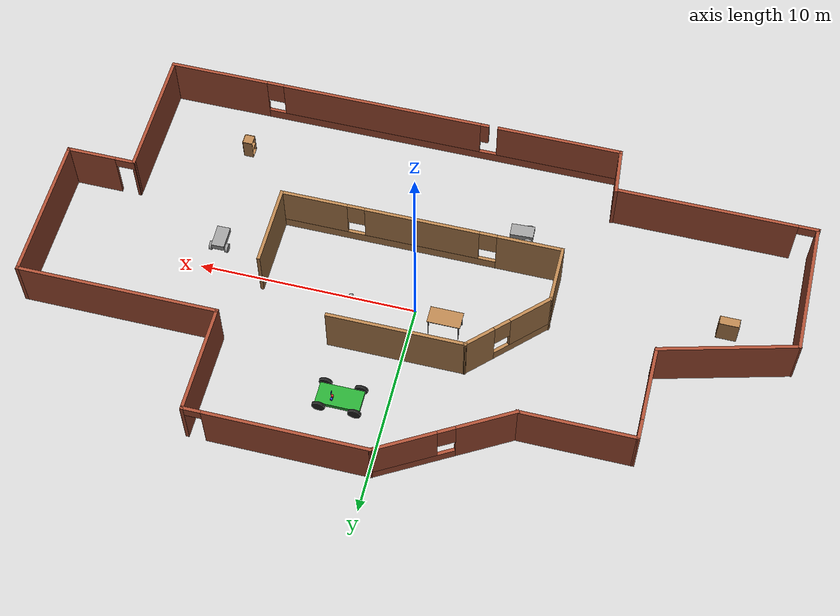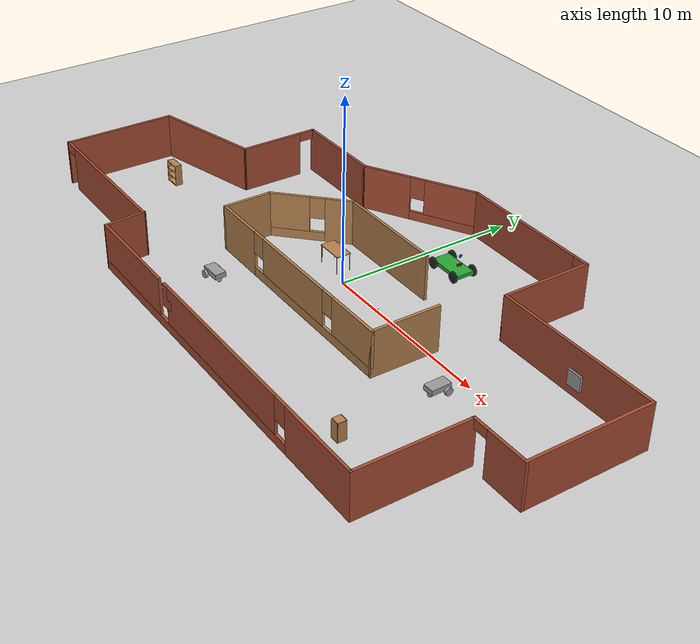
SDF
<sdf version="1.6">
 <world name="default">
  <plugin name="welcome" filename="libwelcome.so"/>
  <light name="sun" type="directional">
   <pose>0 0 10 0 -0 0</pose>
   <diffuse>0.8 0.8 0.8 1</diffuse>
   <specular>0.2 0.2 0.2 1</specular>
   <attenuation>
    <range>1000</range>
    <constant>0.9</constant>
    <linear>0.01</linear>
    <quadratic>0.001</quadratic>
   </attenuation>
   <direction>-0.5 0.1 -0.9</direction>
  </light>
  <model name="ground_plane">
   <static>1</static>
   <link name="link">
    <collision name="collision">
     <geometry><plane><normal>0 0 1</normal><size>100 100</size></plane></geometry>
     <surface>
      <contact><collide_bitmask>65535</collide_bitmask></contact>
      <friction><ode><mu>100</mu><mu2>50</mu2></ode></friction>
     </surface>
    </collision>
    <visual name="visual">
     <cast_shadows>0</cast_shadows>
     <geometry><plane><normal>0 0 1</normal><size>100 100</size></plane></geometry>
     <material>
      <script><uri>file://media/materials/scripts/gazebo.material</uri><name>Gazebo/Grey</name></script>
     </material>
    </visual>
   </link>
  </model>
  <gravity>0 0 -9.8</gravity>
  <magnetic_field>6e-06 2.3e-05 -4.2e-05</magnetic_field>
  <atmosphere type="adiabatic"/>
  <physics name="default_physics" default="0" type="ode">
   <max_step_size>0.001</max_step_size>
   <real_time_factor>1</real_time_factor>
   <real_time_update_rate>1000</real_time_update_rate>
  </physics>
  <scene><ambient>0.4 0.4 0.4 1</ambient><background>0.7 0.7 0.7 1</background><shadows>1</shadows></scene>
  <spherical_coordinates>
   <surface_model>EARTH_WGS84</surface_model>
   <latitude_deg>0</latitude_deg>
   <longitude_deg>0</longitude_deg>
   <elevation>0</elevation>
   <heading_deg>0</heading_deg>
  </spherical_coordinates>
  <model name="office">
   <pose>0.19118 -0.3324 0 0 -0 0</pose>
   <link name="Wall_10">
    <pose>3.71196 8.6392 0 0 -0 0</pose>
    <visual name="Wall_10_Visual_0">
     <pose>-0.451666 0 1.25 0 -0 0</pose>
     <geometry><box><size>7.34667 0.15 2.5</size></box></geometry>
     <material>
      <script><uri>file://media/materials/scripts/gazebo.material</uri><name>Gazebo/Bricks</name></script>
      <ambient>1 1 1 1</ambient>
     </material>
     <meta><layer>0</layer></meta>
    </visual>
    <collision name="Wall_10_Collision_0">
     <geometry><box><size>7.34667 0.15 2.5</size></box></geometry>
     <pose>-0.451666 0 1.25 0 -0 0</pose>
    </collision>
    <visual name="Wall_10_Visual_1">
     <pose>4.12333 0 1.25 0 -0 0</pose>
     <geometry><box><size>0.003332 0.15 2.5</size></box></geometry>
     <material>
      <script><uri>file://media/materials/scripts/gazebo.material</uri><name>Gazebo/Bricks</name></script>
      <ambient>1 1 1 1</ambient>
     </material>
     <meta><layer>0</layer></meta>
    </visual>
    <collision name="Wall_10_Collision_1">
     <geometry><box><size>0.003332 0.15 2.5</size></box></geometry>
     <pose>4.12333 0 1.25 0 -0 0</pose>
    </collision>
    <visual name="Wall_10_Visual_2">
     <pose>3.67167 0 2.25 0 -0 0</pose>
     <geometry><box><size>0.9 0.15 0.5</size></box></geometry>
     <material>
      <script><uri>file://media/materials/scripts/gazebo.material</uri><name>Gazebo/Bricks</name></script>
      <ambient>1 1 1 1</ambient>
     </material>
     <meta><layer>0</layer></meta>
    </visual>
    <collision name="Wall_10_Collision_2">
     <geometry><box><size>0.9 0.15 0.5</size></box></geometry>
     <pose>3.67167 0 2.25 0 -0 0</pose>
    </collision>
   </link>
   <link name="Wall_11">
    <collision name="Wall_11_Collision">
     <geometry><box><size>5 0.15 2.5</size></box></geometry>
     <pose>0 0 1.25 0 -0 0</pose>
    </collision>
    <visual name="Wall_11_Visual">
     <pose>0 0 1.25 0 -0 0</pose>
     <geometry><box><size>5 0.15 2.5</size></box></geometry>
     <material>
      <script><uri>file://media/materials/scripts/gazebo.material</uri><name>Gazebo/Bricks</name></script>
      <ambient>0.435294 0.796078 0.67451 1</ambient>
     </material>
     <meta><layer>0</layer></meta>
    </visual>
    <pose>7.76196 6.2142 0 0 0 -1.5708</pose>
   </link>
   <link name="Wall_12">
    <collision name="Wall_12_Collision">
     <geometry><box><size>9.25 0.15 2.5</size></box></geometry>
     <pose>0 0 1.25 0 -0 0</pose>
    </collision>
    <visual name="Wall_12_Visual">
     <pose>0 0 1.25 0 -0 0</pose>
     <geometry><box><size>9.25 0.15 2.5</size></box></geometry>
     <material>
      <script><uri>file://media/materials/scripts/gazebo.material</uri><name>Gazebo/Bricks</name></script>
      <ambient>0.435294 0.796078 0.67451 1</ambient>
     </material>
     <meta><layer>0</layer></meta>
    </visual>
    <pose>12.312 3.7892 0 0 -0 0</pose>
   </link>
   <link name="Wall_13">
    <collision name="Wall_13_Collision">
     <geometry><box><size>6.75 0.15 2.5</size></box></geometry>
     <pose>0 0 1.25 0 -0 0</pose>
    </collision>
    <visual name="Wall_13_Visual">
     <pose>0 0 1.25 0 -0 0</pose>
     <geometry><box><size>6.75 0.15 2.5</size></box></geometry>
     <material>
      <script><uri>file://media/materials/scripts/gazebo.material</uri><name>Gazebo/Bricks</name></script>
      <ambient>0.435294 0.796078 0.67451 1</ambient>
     </material>
     <meta><layer>0</layer></meta>
    </visual>
    <pose>16.862 0.489204 0 0 0 -1.5708</pose>
   </link>
   <link name="Wall_14">
    <pose>15.312 -2.8108 0 0 -0 3.14159</pose>
    <visual name="Wall_14_Visual_0">
     <pose>-0.469815 0 1.25 0 -0 0</pose>
     <geometry><box><size>2.31037 0.15 2.5</size></box></geometry>
     <material>
      <script><uri>file://media/materials/scripts/gazebo.material</uri><name>Gazebo/Bricks</name></script>
      <ambient>0.435294 0.796078 0.67451 1</ambient>
     </material>
     <meta><layer>0</layer></meta>
    </visual>
    <collision name="Wall_14_Collision_0">
     <geometry><box><size>2.31037 0.15 2.5</size></box></geometry>
     <pose>-0.469815 0 1.25 0 -0 0</pose>
    </collision>
    <visual name="Wall_14_Visual_1">
     <pose>1.60519 0 1.25 0 -0 0</pose>
     <geometry><box><size>0.03963 0.15 2.5</size></box></geometry>
     <material>
      <script><uri>file://media/materials/scripts/gazebo.material</uri><name>Gazebo/Bricks</name></script>
      <ambient>0.435294 0.796078 0.67451 1</ambient>
     </material>
     <meta><layer>0</layer></meta>
    </visual>
    <collision name="Wall_14_Collision_1">
     <geometry><box><size>0.03963 0.15 2.5</size></box></geometry>
     <pose>1.60519 0 1.25 0 -0 0</pose>
    </collision>
    <visual name="Wall_14_Visual_2">
     <pose>1.13537 0 2.25 0 -0 0</pose>
     <geometry><box><size>0.9 0.15 0.5</size></box></geometry>
     <material>
      <script><uri>file://media/materials/scripts/gazebo.material</uri><name>Gazebo/Bricks</name></script>
      <ambient>0.435294 0.796078 0.67451 1</ambient>
     </material>
     <meta><layer>0</layer></meta>
    </visual>
    <collision name="Wall_14_Collision_2">
     <geometry><box><size>0.9 0.15 0.5</size></box></geometry>
     <pose>1.13537 0 2.25 0 -0 0</pose>
    </collision>
   </link>
   <link name="Wall_15">
    <collision name="Wall_15_Collision">
     <geometry><box><size>6 0.15 2.5</size></box></geometry>
     <pose>0 0 1.25 0 -0 0</pose>
    </collision>
    <visual name="Wall_15_Visual">
     <pose>0 0 1.25 0 -0 0</pose>
     <geometry><box><size>6 0.15 2.5</size></box></geometry>
     <material>
      <script><uri>file://media/materials/scripts/gazebo.material</uri><name>Gazebo/Bricks</name></script>
      <ambient>0.435294 0.796078 0.67451 1</ambient>
     </material>
     <meta><layer>0</layer></meta>
    </visual>
    <pose>13.762 -5.7358 0 0 0 -1.5708</pose>
   </link>
   <link name="Wall_16">
    <pose>3.08696 -8.6608 0 0 -0 3.14159</pose>
    <visual name="Wall_16_Visual_0">
     <pose>-8.41899 0 1.25 0 -0 0</pose>
     <geometry><box><size>4.66203 0.15 2.5</size></box></geometry>
     <material>
      <script><uri>file://media/materials/scripts/gazebo.material</uri><name>Gazebo/Bricks</name></script>
      <ambient>0.435294 0.796078 0.67451 1</ambient>
     </material>
     <meta><layer>0</layer></meta>
    </visual>
    <collision name="Wall_16_Collision_0">
     <geometry><box><size>4.66203 0.15 2.5</size></box></geometry>
     <pose>-8.41899 0 1.25 0 -0 0</pose>
    </collision>
    <visual name="Wall_16_Visual_1">
     <pose>2.33101 0 0.25 0 -0 0</pose>
     <geometry><box><size>16.838 0.15 0.5</size></box></geometry>
     <material>
      <script><uri>file://media/materials/scripts/gazebo.material</uri><name>Gazebo/Bricks</name></script>
      <ambient>0.435294 0.796078 0.67451 1</ambient>
     </material>
     <meta><layer>0</layer></meta>
    </visual>
    <collision name="Wall_16_Collision_1">
     <geometry><box><size>16.838 0.15 0.5</size></box></geometry>
     <pose>2.33101 0 0.25 0 -0 0</pose>
    </collision>
    <visual name="Wall_16_Visual_2">
     <pose>-0.576441 0 1.5 0 -0 0</pose>
     <geometry><box><size>9.42306 0.15 2</size></box></geometry>
     <material>
      <script><uri>file://media/materials/scripts/gazebo.material</uri><name>Gazebo/Bricks</name></script>
      <ambient>0.435294 0.796078 0.67451 1</ambient>
     </material>
     <meta><layer>0</layer></meta>
    </visual>
    <collision name="Wall_16_Collision_2">
     <geometry><box><size>9.42306 0.15 2</size></box></geometry>
     <pose>-0.576441 0 1.5 0 -0 0</pose>
    </collision>
    <visual name="Wall_16_Visual_3">
     <pose>7.84255 0 1.5 0 -0 0</pose>
     <geometry><box><size>5.81491 0.15 2</size></box></geometry>
     <material>
      <script><uri>file://media/materials/scripts/gazebo.material</uri><name>Gazebo/Bricks</name></script>
      <ambient>0.435294 0.796078 0.67451 1</ambient>
     </material>
     <meta><layer>0</layer></meta>
    </visual>
    <collision name="Wall_16_Collision_3">
     <geometry><box><size>5.81491 0.15 2</size></box></geometry>
     <pose>7.84255 0 1.5 0 -0 0</pose>
    </collision>
    <visual name="Wall_16_Visual_4">
     <pose>-5.68797 0 1.9 0 -0 0</pose>
     <geometry><box><size>0.8 0.15 1.2</size></box></geometry>
     <material>
      <script><uri>file://media/materials/scripts/gazebo.material</uri><name>Gazebo/Bricks</name></script>
      <ambient>0.435294 0.796078 0.67451 1</ambient>
     </material>
     <meta><layer>0</layer></meta>
    </visual>
    <collision name="Wall_16_Collision_4">
     <geometry><box><size>0.8 0.15 1.2</size></box></geometry>
     <pose>-5.68797 0 1.9 0 -0 0</pose>
    </collision>
    <visual name="Wall_16_Visual_5">
     <pose>4.13509 0 1.9 0 -0 0</pose>
     <geometry><box><size>0.8 0.15 1.2</size></box></geometry>
     <material>
      <script><uri>file://media/materials/scripts/gazebo.material</uri><name>Gazebo/Bricks</name></script>
      <ambient>0.435294 0.796078 0.67451 1</ambient>
     </material>
     <meta><layer>0</layer></meta>
    </visual>
    <collision name="Wall_16_Collision_5">
     <geometry><box><size>0.8 0.15 1.2</size></box></geometry>
     <pose>4.13509 0 1.9 0 -0 0</pose>
    </collision>
   </link>
   <link name="Wall_17">
    <collision name="Wall_17_Collision">
     <geometry><box><size>2.28536 0.15 2.5</size></box></geometry>
     <pose>0 0 1.25 0 -0 0</pose>
    </collision>
    <visual name="Wall_17_Visual">
     <pose>0 0 1.25 0 -0 0</pose>
     <geometry><box><size>2.28536 0.15 2.5</size></box></geometry>
     <material>
      <script><uri>file://media/materials/scripts/gazebo.material</uri><name>Gazebo/Bricks</name></script>
      <ambient>0.435294 0.796078 0.67451 1</ambient>
     </material>
     <meta><layer>0</layer></meta>
    </visual>
    <pose>-7.675 -7.59667 0 0 -0 1.65233</pose>
   </link>
   <link name="Wall_18">
    <pose>-12.312 -6.56732 0 0 -0 3.14159</pose>
    <visual name="Wall_18_Visual_0">
     <pose>-0.488616 0 1.25 0 -0 0</pose>
     <geometry><box><size>8.27277 0.15 2.5</size></box></geometry>
     <material>
      <script><uri>file://media/materials/scripts/gazebo.material</uri><name>Gazebo/Bricks</name></script>
      <ambient>0.435294 0.796078 0.67451 1</ambient>
     </material>
     <meta><layer>0</layer></meta>
    </visual>
    <collision name="Wall_18_Collision_0">
     <geometry><box><size>8.27277 0.15 2.5</size></box></geometry>
     <pose>-0.488616 0 1.25 0 -0 0</pose>
    </collision>
    <visual name="Wall_18_Visual_1">
     <pose>4.58638 0 1.25 0 -0 0</pose>
     <geometry><box><size>0.077231 0.15 2.5</size></box></geometry>
     <material>
      <script><uri>file://media/materials/scripts/gazebo.material</uri><name>Gazebo/Bricks</name></script>
      <ambient>0.435294 0.796078 0.67451 1</ambient>
     </material>
     <meta><layer>0</layer></meta>
    </visual>
    <collision name="Wall_18_Collision_1">
     <geometry><box><size>0.077231 0.15 2.5</size></box></geometry>
     <pose>4.58638 0 1.25 0 -0 0</pose>
    </collision>
    <visual name="Wall_18_Visual_2">
     <pose>4.09777 0 2.25 0 -0 0</pose>
     <geometry><box><size>0.9 0.15 0.5</size></box></geometry>
     <material>
      <script><uri>file://media/materials/scripts/gazebo.material</uri><name>Gazebo/Bricks</name></script>
      <ambient>0.435294 0.796078 0.67451 1</ambient>
     </material>
     <meta><layer>0</layer></meta>
    </visual>
    <collision name="Wall_18_Collision_2">
     <geometry><box><size>0.9 0.15 0.5</size></box></geometry>
     <pose>4.09777 0 2.25 0 -0 0</pose>
    </collision>
   </link>
   <link name="Wall_21">
    <pose>-4.52938 1.29817 0 0 0 -2.35619</pose>
    <visual name="Wall_21_Visual_0">
     <pose>-1.48243 0 1.25 0 -0 0</pose>
     <geometry><box><size>1.53513 0.15 2.5</size></box></geometry>
     <material>
      <script><uri>file://media/materials/scripts/gazebo.material</uri><name>Gazebo/Wood</name></script>
      <ambient>0.435294 0.796078 0.67451 1</ambient>
     </material>
     <meta><layer>0</layer></meta>
    </visual>
    <collision name="Wall_21_Collision_0">
     <geometry><box><size>1.53513 0.15 2.5</size></box></geometry>
     <pose>-1.48243 0 1.25 0 -0 0</pose>
    </collision>
    <visual name="Wall_21_Visual_1">
     <pose>0.767566 0 0.25 0 -0 0</pose>
     <geometry><box><size>2.96487 0.15 0.5</size></box></geometry>
     <material>
      <script><uri>file://media/materials/scripts/gazebo.material</uri><name>Gazebo/Wood</name></script>
      <ambient>0.435294 0.796078 0.67451 1</ambient>
     </material>
     <meta><layer>0</layer></meta>
    </visual>
    <collision name="Wall_21_Collision_1">
     <geometry><box><size>2.96487 0.15 0.5</size></box></geometry>
     <pose>0.767566 0 0.25 0 -0 0</pose>
    </collision>
    <visual name="Wall_21_Visual_2">
     <pose>1.16757 0 1.5 0 -0 0</pose>
     <geometry><box><size>2.16487 0.15 2</size></box></geometry>
     <material>
      <script><uri>file://media/materials/scripts/gazebo.material</uri><name>Gazebo/Wood</name></script>
      <ambient>0.435294 0.796078 0.67451 1</ambient>
     </material>
     <meta><layer>0</layer></meta>
    </visual>
    <collision name="Wall_21_Collision_2">
     <geometry><box><size>2.16487 0.15 2</size></box></geometry>
     <pose>1.16757 0 1.5 0 -0 0</pose>
    </collision>
    <visual name="Wall_21_Visual_3">
     <pose>-0.314868 0 1.9 0 -0 0</pose>
     <geometry><box><size>0.8 0.15 1.2</size></box></geometry>
     <material>
      <script><uri>file://media/materials/scripts/gazebo.material</uri><name>Gazebo/Wood</name></script>
      <ambient>0.435294 0.796078 0.67451 1</ambient>
     </material>
     <meta><layer>0</layer></meta>
    </visual>
    <collision name="Wall_21_Collision_3">
     <geometry><box><size>0.8 0.15 1.2</size></box></geometry>
     <pose>-0.314868 0 1.9 0 -0 0</pose>
    </collision>
   </link>
   <link name="Wall_22">
    <collision name="Wall_22_Collision">
     <geometry><box><size>2.75 0.15 2.5</size></box></geometry>
     <pose>0 0 1.25 0 -0 0</pose>
    </collision>
    <visual name="Wall_22_Visual">
     <pose>0 0 1.25 0 -0 0</pose>
     <geometry><box><size>2.75 0.15 2.5</size></box></geometry>
     <material>
      <script><uri>file://media/materials/scripts/gazebo.material</uri><name>Gazebo/Wood</name></script>
      <ambient>0.435294 0.796078 0.67451 1</ambient>
     </material>
     <meta><layer>0</layer></meta>
    </visual>
    <pose>-6.06734 -1.53979 0 0 0 -1.5708</pose>
   </link>
   <link name="Wall_23">
    <pose>0.357662 -2.83979 0 0 -0 0</pose>
    <visual name="Wall_23_Visual_0">
     <pose>-4.98806 0 1.25 0 -0 0</pose>
     <geometry><box><size>3.02388 0.15 2.5</size></box></geometry>
     <material>
      <script><uri>file://media/materials/scripts/gazebo.material</uri><name>Gazebo/Wood</name></script>
      <ambient>0.435294 0.796078 0.67451 1</ambient>
     </material>
     <meta><layer>0</layer></meta>
    </visual>
    <collision name="Wall_23_Collision_0">
     <geometry><box><size>3.02388 0.15 2.5</size></box></geometry>
     <pose>-4.98806 0 1.25 0 -0 0</pose>
    </collision>
    <visual name="Wall_23_Visual_1">
     <pose>1.51194 0 0.25 0 -0 0</pose>
     <geometry><box><size>9.97612 0.15 0.5</size></box></geometry>
     <material>
      <script><uri>file://media/materials/scripts/gazebo.material</uri><name>Gazebo/Wood</name></script>
      <ambient>0.435294 0.796078 0.67451 1</ambient>
     </material>
     <meta><layer>0</layer></meta>
    </visual>
    <collision name="Wall_23_Collision_1">
     <geometry><box><size>9.97612 0.15 0.5</size></box></geometry>
     <pose>1.51194 0 0.25 0 -0 0</pose>
    </collision>
    <visual name="Wall_23_Visual_2">
     <pose>-0.051543 0 1.5 0 -0 0</pose>
     <geometry><box><size>5.24915 0.15 2</size></box></geometry>
     <material>
      <script><uri>file://media/materials/scripts/gazebo.material</uri><name>Gazebo/Wood</name></script>
      <ambient>0.435294 0.796078 0.67451 1</ambient>
     </material>
     <meta><layer>0</layer></meta>
    </visual>
    <collision name="Wall_23_Collision_2">
     <geometry><box><size>5.24915 0.15 2</size></box></geometry>
     <pose>-0.051543 0 1.5 0 -0 0</pose>
    </collision>
    <visual name="Wall_23_Visual_3">
     <pose>4.93652 0 1.5 0 -0 0</pose>
     <geometry><box><size>3.12697 0.15 2</size></box></geometry>
     <material>
      <script><uri>file://media/materials/scripts/gazebo.material</uri><name>Gazebo/Wood</name></script>
      <ambient>0.435294 0.796078 0.67451 1</ambient>
     </material>
     <meta><layer>0</layer></meta>
    </visual>
    <collision name="Wall_23_Collision_3">
     <geometry><box><size>3.12697 0.15 2</size></box></geometry>
     <pose>4.93652 0 1.5 0 -0 0</pose>
    </collision>
    <visual name="Wall_23_Visual_4">
     <pose>-3.07612 0 1.9 0 -0 0</pose>
     <geometry><box><size>0.8 0.15 1.2</size></box></geometry>
     <material>
      <script><uri>file://media/materials/scripts/gazebo.material</uri><name>Gazebo/Wood</name></script>
      <ambient>0.435294 0.796078 0.67451 1</ambient>
     </material>
     <meta><layer>0</layer></meta>
    </visual>
    <collision name="Wall_23_Collision_4">
     <geometry><box><size>0.8 0.15 1.2</size></box></geometry>
     <pose>-3.07612 0 1.9 0 -0 0</pose>
    </collision>
    <visual name="Wall_23_Visual_5">
     <pose>2.97303 0 1.9 0 -0 0</pose>
     <geometry><box><size>0.8 0.15 1.2</size></box></geometry>
     <material>
      <script><uri>file://media/materials/scripts/gazebo.material</uri><name>Gazebo/Wood</name></script>
      <ambient>0.435294 0.796078 0.67451 1</ambient>
     </material>
     <meta><layer>0</layer></meta>
    </visual>
    <collision name="Wall_23_Collision_5">
     <geometry><box><size>0.8 0.15 1.2</size></box></geometry>
     <pose>2.97303 0 1.9 0 -0 0</pose>
    </collision>
   </link>
   <link name="Wall_24">
    <collision name="Wall_24_Collision">
     <geometry><box><size>3.75 0.15 2.5</size></box></geometry>
     <pose>0 0 1.25 0 -0 0</pose>
    </collision>
    <visual name="Wall_24_Visual">
     <pose>0 0 1.25 0 -0 0</pose>
     <geometry><box><size>3.75 0.15 2.5</size></box></geometry>
     <material>
      <script><uri>file://media/materials/scripts/gazebo.material</uri><name>Gazebo/Wood</name></script>
      <ambient>0.435294 0.796078 0.67451 1</ambient>
     </material>
     <meta><layer>0</layer></meta>
    </visual>
    <pose>6.78266 -1.03979 0 0 -0 1.5708</pose>
   </link>
   <link name="Wall_27">
    <collision name="Wall_27_Collision">
     <geometry><box><size>6.25 0.15 2.5</size></box></geometry>
     <pose>0 0 1.25 0 -0 0</pose>
    </collision>
    <visual name="Wall_27_Visual">
     <pose>0 0 1.25 0 -0 0</pose>
     <geometry><box><size>6.25 0.15 2.5</size></box></geometry>
     <material>
      <script><uri>file://media/materials/scripts/gazebo.material</uri><name>Gazebo/Wood</name></script>
      <ambient>0.435294 0.796078 0.67451 1</ambient>
     </material>
     <meta><layer>0</layer></meta>
    </visual>
    <pose>0.058577 2.83612 0 0 -0 0</pose>
   </link>
   <link name="Wall_5">
    <collision name="Wall_5_Collision">
     <geometry><box><size>6.25 0.15 2.5</size></box></geometry>
     <pose>0 0 1.25 0 -0 0</pose>
    </collision>
    <visual name="Wall_5_Visual">
     <pose>0 0 1.25 0 -0 0</pose>
     <geometry><box><size>6.25 0.15 2.5</size></box></geometry>
     <material>
      <script><uri>file://media/materials/scripts/gazebo.material</uri><name>Gazebo/Bricks</name></script>
      <ambient>0.435294 0.796078 0.67451 1</ambient>
     </material>
     <meta><layer>0</layer></meta>
    </visual>
    <pose>-16.8295 -3.51459 0 0 -0 1.5708</pose>
   </link>
   <link name="Wall_6">
    <collision name="Wall_6_Collision">
     <geometry><box><size>6.25 0.15 2.5</size></box></geometry>
     <pose>0 0 1.25 0 -0 0</pose>
    </collision>
    <visual name="Wall_6_Visual">
     <pose>0 0 1.25 0 -0 0</pose>
     <geometry><box><size>6.25 0.15 2.5</size></box></geometry>
     <material>
      <script><uri>file://media/materials/scripts/gazebo.material</uri><name>Gazebo/Bricks</name></script>
      <ambient>0.435294 0.796078 0.67451 1</ambient>
     </material>
     <meta><layer>0</layer></meta>
    </visual>
    <pose>-13.8834 0.324806 0 0 -0 0.261799</pose>
   </link>
   <link name="Wall_7">
    <pose>-10.9373 3.2892 0 0 -0 1.5708</pose>
    <visual name="Wall_7_Visual_0">
     <pose>-0.480218 0 1.25 0 -0 0</pose>
     <geometry><box><size>3.53957 0.15 2.5</size></box></geometry>
     <material>
      <script><uri>file://media/materials/scripts/gazebo.material</uri><name>Gazebo/Bricks</name></script>
      <ambient>0.435294 0.796078 0.67451 1</ambient>
     </material>
     <meta><layer>0</layer></meta>
    </visual>
    <collision name="Wall_7_Collision_0">
     <geometry><box><size>3.53957 0.15 2.5</size></box></geometry>
     <pose>-0.480218 0 1.25 0 -0 0</pose>
    </collision>
    <visual name="Wall_7_Visual_1">
     <pose>2.21978 0 1.25 0 -0 0</pose>
     <geometry><box><size>0.060435 0.15 2.5</size></box></geometry>
     <material>
      <script><uri>file://media/materials/scripts/gazebo.material</uri><name>Gazebo/Bricks</name></script>
      <ambient>0.435294 0.796078 0.67451 1</ambient>
     </material>
     <meta><layer>0</layer></meta>
    </visual>
    <collision name="Wall_7_Collision_1">
     <geometry><box><size>0.060435 0.15 2.5</size></box></geometry>
     <pose>2.21978 0 1.25 0 -0 0</pose>
    </collision>
    <visual name="Wall_7_Visual_2">
     <pose>1.73957 0 2.25 0 -0 0</pose>
     <geometry><box><size>0.9 0.15 0.5</size></box></geometry>
     <material>
      <script><uri>file://media/materials/scripts/gazebo.material</uri><name>Gazebo/Bricks</name></script>
      <ambient>0.435294 0.796078 0.67451 1</ambient>
     </material>
     <meta><layer>0</layer></meta>
    </visual>
    <collision name="Wall_7_Collision_2">
     <geometry><box><size>0.9 0.15 0.5</size></box></geometry>
     <pose>1.73957 0 2.25 0 -0 0</pose>
    </collision>
   </link>
   <link name="Wall_8">
    <collision name="Wall_8_Collision">
     <geometry><box><size>5.25 0.15 2.5</size></box></geometry>
     <pose>0 0 1.25 0 -0 0</pose>
    </collision>
    <visual name="Wall_8_Visual">
     <pose>0 0 1.25 0 -0 0</pose>
     <geometry><box><size>5.25 0.15 2.5</size></box></geometry>
     <material>
      <script><uri>file://media/materials/scripts/gazebo.material</uri><name>Gazebo/Bricks</name></script>
      <ambient>0.435294 0.796078 0.67451 1</ambient>
     </material>
     <meta><layer>0</layer></meta>
    </visual>
    <pose>-8.3873 5.4642 0 0 -0 0</pose>
   </link>
   <link name="Wall_9">
    <pose>-3.08767 7.0517 0 0 -0 0.523599</pose>
    <visual name="Wall_9_Visual_0">
     <pose>-1.86997 0 1.25 0 -0 0</pose>
     <geometry><box><size>2.76007 0.15 2.5</size></box></geometry>
     <material>
      <script><uri>file://media/materials/scripts/gazebo.material</uri><name>Gazebo/Bricks</name></script>
      <ambient>0.435294 0.796078 0.67451 1</ambient>
     </material>
     <meta><layer>0</layer></meta>
    </visual>
    <collision name="Wall_9_Collision_0">
     <geometry><box><size>2.76007 0.15 2.5</size></box></geometry>
     <pose>-1.86997 0 1.25 0 -0 0</pose>
    </collision>
    <visual name="Wall_9_Visual_1">
     <pose>1.38003 0 0.25 0 -0 0</pose>
     <geometry><box><size>3.73993 0.15 0.5</size></box></geometry>
     <material>
      <script><uri>file://media/materials/scripts/gazebo.material</uri><name>Gazebo/Bricks</name></script>
      <ambient>0.435294 0.796078 0.67451 1</ambient>
     </material>
     <meta><layer>0</layer></meta>
    </visual>
    <collision name="Wall_9_Collision_1">
     <geometry><box><size>3.73993 0.15 0.5</size></box></geometry>
     <pose>1.38003 0 0.25 0 -0 0</pose>
    </collision>
    <visual name="Wall_9_Visual_2">
     <pose>1.78003 0 1.5 0 -0 0</pose>
     <geometry><box><size>2.93993 0.15 2</size></box></geometry>
     <material>
      <script><uri>file://media/materials/scripts/gazebo.material</uri><name>Gazebo/Bricks</name></script>
      <ambient>0.435294 0.796078 0.67451 1</ambient>
     </material>
     <meta><layer>0</layer></meta>
    </visual>
    <collision name="Wall_9_Collision_2">
     <geometry><box><size>2.93993 0.15 2</size></box></geometry>
     <pose>1.78003 0 1.5 0 -0 0</pose>
    </collision>
    <visual name="Wall_9_Visual_3">
     <pose>-0.089932 0 1.9 0 -0 0</pose>
     <geometry><box><size>0.8 0.15 1.2</size></box></geometry>
     <material>
      <script><uri>file://media/materials/scripts/gazebo.material</uri><name>Gazebo/Bricks</name></script>
      <ambient>0.435294 0.796078 0.67451 1</ambient>
     </material>
     <meta><layer>0</layer></meta>
    </visual>
    <collision name="Wall_9_Collision_3">
     <geometry><box><size>0.8 0.15 1.2</size></box></geometry>
     <pose>-0.089932 0 1.9 0 -0 0</pose>
    </collision>
   </link>
   <link name="Window_3">
    <collision name="Window_3_Collision">
     <geometry><box><size>0.8 0.17 0.8</size></box></geometry>
     <pose>0 0 0.4 0 -0 0</pose>
    </collision>
    <visual name="Window_3_Visual">
     <pose>0 0 0.4 0 -0 0</pose>
     <geometry><box><size>0.8 0.17 0.8</size></box></geometry>
     <material>
      <script><uri>file://media/materials/scripts/gazebo.material</uri><name>Gazebo/Grey</name></script>
     </material>
    </visual>
    <pose>12.6464 3.683 0.5 0 -0 0</pose>
   </link>
   <static>1</static>
  </model>
  <model name="cart">
   <link name="link_0">
    <pose>0.000334 -0.065586 0.044669 0 -0 0</pose>
    <inertial>
     <mass>0.183478</mass>
     <inertia>
      <ixx>0.0186131</ixx>
      <ixy>0</ixy>
      <ixz>0</ixz>
      <iyy>0.00678768</iyy>
      <iyz>0</iyz>
      <izz>0.0228966</izz>
     </inertia>
    </inertial>
    <visual name="visual">
     <pose>0 0 0.2 0 -0 0</pose>
     <geometry><box><size>0.6017 1.06558 0.286166</size></box></geometry>
     <material>
      <lighting>1</lighting>
      <script><uri>file://media/materials/scripts/gazebo.material</uri><name>Gazebo/Grey</name></script>
      <shader type="pixel"><normal_map>__default__</normal_map></shader>
      <ambient>0.3 0.3 0.3 1</ambient>
      <diffuse>0.7 0.7 0.7 1</diffuse>
      <specular>0.01 0.01 0.01 1</specular>
      <emissive>0 0 0 1</emissive>
     </material>
    </visual>
    <collision name="collision">
     <pose>0 0 0.2 0 -0 0</pose>
     <geometry><box><size>0.6017 1.06558 0.286166</size></box></geometry>
     <surface>
      <friction>
       <ode><mu>1</mu><mu2>1</mu2><fdir1>0 0 0</fdir1><slip1>0</slip1><slip2>0</slip2></ode>
       <torsional>
        <coefficient>1</coefficient>
        <patch_radius>0</patch_radius>
        <surface_radius>0</surface_radius>
        <use_patch_radius>1</use_patch_radius>
        <ode><slip>0</slip></ode>
       </torsional>
      </friction>
      <bounce><restitution_coefficient>0</restitution_coefficient><threshold>1e+06</threshold></bounce>
      <contact>
       <collide_without_contact>0</collide_without_contact>
       <collide_without_contact_bitmask>1</collide_without_contact_bitmask>
       <collide_bitmask>1</collide_bitmask>
       <ode>
        <soft_cfm>0</soft_cfm>
        <soft_erp>0.2</soft_erp>
        <kp>1e+13</kp>
        <kd>1</kd>
        <max_vel>0.01</max_vel>
        <min_depth>0</min_depth>
       </ode>
       <bullet>
        <split_impulse>1</split_impulse>
        <split_impulse_penetration_threshold>-0.01</split_impulse_penetration_threshold>
        <soft_cfm>0</soft_cfm>
        <soft_erp>0.2</soft_erp>
        <kp>1e+13</kp>
        <kd>1</kd>
       </bullet>
      </contact>
     </surface>
    </collision>
   </link>
   <link name="link_1">
    <pose>-0.001 -0.462788 -0.129729 0 -0 0</pose>
    <inertial>
     <mass>1.886</mass>
     <inertia>
      <ixx>0.0115145</ixx>
      <ixy>0</ixy>
      <ixz>0</ixz>
      <iyy>0.0115145</iyy>
      <iyz>0</iyz>
      <izz>0.0115145</izz>
     </inertia>
     <pose>0 0 0.024704 0 -0 0</pose>
    </inertial>
    <visual name="visual">
     <pose>0 0 0.1 0 -0 0</pose>
     <geometry><sphere><radius>0.123544</radius></sphere></geometry>
     <material>
      <lighting>1</lighting>
      <script><uri>file://media/materials/scripts/gazebo.material</uri><name>Gazebo/Grey</name></script>
      <shader type="pixel"><normal_map>__default__</normal_map></shader>
      <ambient>0.3 0.3 0.3 1</ambient>
      <diffuse>0.7 0.7 0.7 1</diffuse>
      <specular>0.01 0.01 0.01 1</specular>
      <emissive>0 0 0 1</emissive>
     </material>
    </visual>
    <collision name="collision">
     <pose>0 0 0.1 0 -0 0</pose>
     <geometry><sphere><radius>0.123544</radius></sphere></geometry>
     <surface>
      <friction>
       <ode><mu>1</mu><mu2>1</mu2><fdir1>0 0 0</fdir1><slip1>0</slip1><slip2>0</slip2></ode>
       <torsional>
        <coefficient>1</coefficient>
        <patch_radius>0</patch_radius>
        <surface_radius>0</surface_radius>
        <use_patch_radius>1</use_patch_radius>
        <ode><slip>0</slip></ode>
       </torsional>
      </friction>
      <bounce><restitution_coefficient>0</restitution_coefficient><threshold>1e+06</threshold></bounce>
      <contact>
       <collide_without_contact>0</collide_without_contact>
       <collide_without_contact_bitmask>1</collide_without_contact_bitmask>
       <collide_bitmask>1</collide_bitmask>
       <ode>
        <soft_cfm>0</soft_cfm>
        <soft_erp>0.2</soft_erp>
        <kp>1e+13</kp>
        <kd>1</kd>
        <max_vel>0.01</max_vel>
        <min_depth>0</min_depth>
       </ode>
       <bullet>
        <split_impulse>1</split_impulse>
        <split_impulse_penetration_threshold>-0.01</split_impulse_penetration_threshold>
        <soft_cfm>0</soft_cfm>
        <soft_erp>0.2</soft_erp>
        <kp>1e+13</kp>
        <kd>1</kd>
       </bullet>
      </contact>
     </surface>
    </collision>
   </link>
   <link name="link_2">
    <pose>0.368986 0.26419 0.04253 3.14159 1.55999 3.14159</pose>
    <inertial>
     <mass>0.0216399</mass>
     <inertia>
      <ixx>0.000254029</ixx>
      <ixy>0</ixy>
      <ixz>0</ixz>
      <iyy>0.000254029</iyy>
      <iyz>0</iyz>
      <izz>0.000445951</izz>
     </inertia>
    </inertial>
    <visual name="visual">
     <geometry><cylinder><radius>0.203016</radius><length>0.131225</length></cylinder></geometry>
     <material>
      <lighting>1</lighting>
      <script><uri>file://media/materials/scripts/gazebo.material</uri><name>Gazebo/Grey</name></script>
      <shader type="pixel"><normal_map>__default__</normal_map></shader>
      <ambient>0.3 0.3 0.3 1</ambient>
      <diffuse>0.7 0.7 0.7 1</diffuse>
      <specular>0.01 0.01 0.01 1</specular>
      <emissive>0 0 0 1</emissive>
     </material>
    </visual>
    <collision name="collision">
     <geometry><cylinder><radius>0.203016</radius><length>0.131225</length></cylinder></geometry>
     <surface>
      <friction>
       <ode><mu>1</mu><mu2>1</mu2><fdir1>0 0 0</fdir1><slip1>0</slip1><slip2>0</slip2></ode>
       <torsional>
        <coefficient>1</coefficient>
        <patch_radius>0</patch_radius>
        <surface_radius>0</surface_radius>
        <use_patch_radius>1</use_patch_radius>
        <ode><slip>0</slip></ode>
       </torsional>
      </friction>
      <bounce><restitution_coefficient>0</restitution_coefficient><threshold>1e+06</threshold></bounce>
      <contact>
       <collide_without_contact>0</collide_without_contact>
       <collide_without_contact_bitmask>1</collide_without_contact_bitmask>
       <collide_bitmask>1</collide_bitmask>
       <ode>
        <soft_cfm>0</soft_cfm>
        <soft_erp>0.2</soft_erp>
        <kp>1e+13</kp>
        <kd>1</kd>
        <max_vel>0.01</max_vel>
        <min_depth>0</min_depth>
       </ode>
       <bullet>
        <split_impulse>1</split_impulse>
        <split_impulse_penetration_threshold>-0.01</split_impulse_penetration_threshold>
        <soft_cfm>0</soft_cfm>
        <soft_erp>0.2</soft_erp>
        <kp>1e+13</kp>
        <kd>1</kd>
       </bullet>
      </contact>
     </surface>
    </collision>
   </link>
   <link name="link_2_clone">
    <pose>-0.368319 0.26419 0.04253 3.14159 1.55999 3.14159</pose>
    <inertial>
     <mass>0.0216399</mass>
     <inertia>
      <ixx>0.000254029</ixx>
      <ixy>0</ixy>
      <ixz>0</ixz>
      <iyy>0.000254029</iyy>
      <iyz>0</iyz>
      <izz>0.000445951</izz>
     </inertia>
    </inertial>
    <visual name="visual">
     <geometry><cylinder><radius>0.203016</radius><length>0.131225</length></cylinder></geometry>
     <material>
      <lighting>1</lighting>
      <script><uri>file://media/materials/scripts/gazebo.material</uri><name>Gazebo/Grey</name></script>
      <shader type="pixel"><normal_map>__default__</normal_map></shader>
      <ambient>0.3 0.3 0.3 1</ambient>
      <diffuse>0.7 0.7 0.7 1</diffuse>
      <specular>0.01 0.01 0.01 1</specular>
      <emissive>0 0 0 1</emissive>
     </material>
    </visual>
    <collision name="collision">
     <geometry><cylinder><radius>0.203016</radius><length>0.131225</length></cylinder></geometry>
     <surface>
      <friction>
       <ode><mu>1</mu><mu2>1</mu2><fdir1>0 0 0</fdir1><slip1>0</slip1><slip2>0</slip2></ode>
       <torsional>
        <coefficient>1</coefficient>
        <patch_radius>0</patch_radius>
        <surface_radius>0</surface_radius>
        <use_patch_radius>1</use_patch_radius>
        <ode><slip>0</slip></ode>
       </torsional>
      </friction>
      <bounce><restitution_coefficient>0</restitution_coefficient><threshold>1e+06</threshold></bounce>
      <contact>
       <collide_without_contact>0</collide_without_contact>
       <collide_without_contact_bitmask>1</collide_without_contact_bitmask>
       <collide_bitmask>1</collide_bitmask>
       <ode>
        <soft_cfm>0</soft_cfm>
        <soft_erp>0.2</soft_erp>
        <kp>1e+13</kp>
        <kd>1</kd>
        <max_vel>0.01</max_vel>
        <min_depth>0</min_depth>
       </ode>
       <bullet>
        <split_impulse>1</split_impulse>
        <split_impulse_penetration_threshold>-0.01</split_impulse_penetration_threshold>
        <soft_cfm>0</soft_cfm>
        <soft_erp>0.2</soft_erp>
        <kp>1e+13</kp>
        <kd>1</kd>
       </bullet>
      </contact>
     </surface>
    </collision>
   </link>
   <joint name="link_0_JOINT_0" type="revolute">
    <parent>link_0</parent>
    <child>link_2</child>
    <axis>
     <xyz>0 0 1</xyz>
     <use_parent_model_frame>0</use_parent_model_frame>
     <limit>
      <lower>-1.79769e+308</lower>
      <upper>1.79769e+308</upper>
      <effort>-1</effort>
      <velocity>-1</velocity>
     </limit>
     <dynamics>
      <spring_reference>0</spring_reference>
      <spring_stiffness>0</spring_stiffness>
      <damping>0</damping>
     </dynamics>
    </axis>
    <physics>
     <ode><limit><cfm>0</cfm><erp>0.2</erp></limit><suspension><cfm>0</cfm><erp>0.2</erp></suspension></ode>
    </physics>
   </joint>
   <joint name="link_0_JOINT_1" type="revolute">
    <parent>link_0</parent>
    <child>link_2_clone</child>
    <axis>
     <xyz>0 0 1</xyz>
     <use_parent_model_frame>0</use_parent_model_frame>
     <limit>
      <lower>-1.79769e+308</lower>
      <upper>1.79769e+308</upper>
      <effort>-1</effort>
      <velocity>-1</velocity>
     </limit>
     <dynamics>
      <spring_reference>0</spring_reference>
      <spring_stiffness>0</spring_stiffness>
      <damping>0</damping>
     </dynamics>
    </axis>
    <physics>
     <ode><limit><cfm>0</cfm><erp>0.2</erp></limit><suspension><cfm>0</cfm><erp>0.2</erp></suspension></ode>
    </physics>
   </joint>
   <joint name="link_0_JOINT_2" type="ball">
    <parent>link_0</parent>
    <child>link_1</child>
    <physics>
     <ode><limit><cfm>0</cfm><erp>0.2</erp></limit><suspension><cfm>0</cfm><erp>0.2</erp></suspension></ode>
    </physics>
   </joint>
   <static>0</static>
   <pose>-3.83609 -5.02982 0.158308 0.01089 -0 1.61547</pose>
  </model>
  <model name="cart_0">
   <link name="link_0">
    <pose>0.000334 -0.065586 0.044669 0 -0 0</pose>
    <inertial>
     <mass>0.183478</mass>
     <inertia>
      <ixx>0.0186131</ixx>
      <ixy>0</ixy>
      <ixz>0</ixz>
      <iyy>0.00678768</iyy>
      <iyz>0</iyz>
      <izz>0.0228966</izz>
     </inertia>
    </inertial>
    <visual name="visual">
     <pose>0 0 0.2 0 -0 0</pose>
     <geometry><box><size>0.6017 1.06558 0.286166</size></box></geometry>
     <material>
      <lighting>1</lighting>
      <script><uri>file://media/materials/scripts/gazebo.material</uri><name>Gazebo/Grey</name></script>
      <shader type="pixel"><normal_map>__default__</normal_map></shader>
      <ambient>0.3 0.3 0.3 1</ambient>
      <diffuse>0.7 0.7 0.7 1</diffuse>
      <specular>0.01 0.01 0.01 1</specular>
      <emissive>0 0 0 1</emissive>
     </material>
    </visual>
    <collision name="collision">
     <pose>0 0 0.2 0 -0 0</pose>
     <geometry><box><size>0.6017 1.06558 0.286166</size></box></geometry>
     <surface>
      <friction>
       <ode><mu>1</mu><mu2>1</mu2><fdir1>0 0 0</fdir1><slip1>0</slip1><slip2>0</slip2></ode>
       <torsional>
        <coefficient>1</coefficient>
        <patch_radius>0</patch_radius>
        <surface_radius>0</surface_radius>
        <use_patch_radius>1</use_patch_radius>
        <ode><slip>0</slip></ode>
       </torsional>
      </friction>
      <bounce><restitution_coefficient>0</restitution_coefficient><threshold>1e+06</threshold></bounce>
      <contact>
       <collide_without_contact>0</collide_without_contact>
       <collide_without_contact_bitmask>1</collide_without_contact_bitmask>
       <collide_bitmask>1</collide_bitmask>
       <ode>
        <soft_cfm>0</soft_cfm>
        <soft_erp>0.2</soft_erp>
        <kp>1e+13</kp>
        <kd>1</kd>
        <max_vel>0.01</max_vel>
        <min_depth>0</min_depth>
       </ode>
       <bullet>
        <split_impulse>1</split_impulse>
        <split_impulse_penetration_threshold>-0.01</split_impulse_penetration_threshold>
        <soft_cfm>0</soft_cfm>
        <soft_erp>0.2</soft_erp>
        <kp>1e+13</kp>
        <kd>1</kd>
       </bullet>
      </contact>
     </surface>
    </collision>
   </link>
   <link name="link_1">
    <pose>-0.001 -0.462788 -0.129729 0 -0 0</pose>
    <inertial>
     <mass>1.886</mass>
     <inertia>
      <ixx>0.0115145</ixx>
      <ixy>0</ixy>
      <ixz>0</ixz>
      <iyy>0.0115145</iyy>
      <iyz>0</iyz>
      <izz>0.0115145</izz>
     </inertia>
     <pose>0 0 0.024704 0 -0 0</pose>
    </inertial>
    <visual name="visual">
     <pose>0 0 0.1 0 -0 0</pose>
     <geometry><sphere><radius>0.123544</radius></sphere></geometry>
     <material>
      <lighting>1</lighting>
      <script><uri>file://media/materials/scripts/gazebo.material</uri><name>Gazebo/Grey</name></script>
      <shader type="pixel"><normal_map>__default__</normal_map></shader>
      <ambient>0.3 0.3 0.3 1</ambient>
      <diffuse>0.7 0.7 0.7 1</diffuse>
      <specular>0.01 0.01 0.01 1</specular>
      <emissive>0 0 0 1</emissive>
     </material>
    </visual>
    <collision name="collision">
     <pose>0 0 0.1 0 -0 0</pose>
     <geometry><sphere><radius>0.123544</radius></sphere></geometry>
     <surface>
      <friction>
       <ode><mu>1</mu><mu2>1</mu2><fdir1>0 0 0</fdir1><slip1>0</slip1><slip2>0</slip2></ode>
       <torsional>
        <coefficient>1</coefficient>
        <patch_radius>0</patch_radius>
        <surface_radius>0</surface_radius>
        <use_patch_radius>1</use_patch_radius>
        <ode><slip>0</slip></ode>
       </torsional>
      </friction>
      <bounce><restitution_coefficient>0</restitution_coefficient><threshold>1e+06</threshold></bounce>
      <contact>
       <collide_without_contact>0</collide_without_contact>
       <collide_without_contact_bitmask>1</collide_without_contact_bitmask>
       <collide_bitmask>1</collide_bitmask>
       <ode>
        <soft_cfm>0</soft_cfm>
        <soft_erp>0.2</soft_erp>
        <kp>1e+13</kp>
        <kd>1</kd>
        <max_vel>0.01</max_vel>
        <min_depth>0</min_depth>
       </ode>
       <bullet>
        <split_impulse>1</split_impulse>
        <split_impulse_penetration_threshold>-0.01</split_impulse_penetration_threshold>
        <soft_cfm>0</soft_cfm>
        <soft_erp>0.2</soft_erp>
        <kp>1e+13</kp>
        <kd>1</kd>
       </bullet>
      </contact>
     </surface>
    </collision>
   </link>
   <link name="link_2">
    <pose>0.368986 0.26419 0.04253 3.14159 1.55999 3.14159</pose>
    <inertial>
     <mass>0.0216399</mass>
     <inertia>
      <ixx>0.000254029</ixx>
      <ixy>0</ixy>
      <ixz>0</ixz>
      <iyy>0.000254029</iyy>
      <iyz>0</iyz>
      <izz>0.000445951</izz>
     </inertia>
    </inertial>
    <visual name="visual">
     <geometry><cylinder><radius>0.203016</radius><length>0.131225</length></cylinder></geometry>
     <material>
      <lighting>1</lighting>
      <script><uri>file://media/materials/scripts/gazebo.material</uri><name>Gazebo/Grey</name></script>
      <shader type="pixel"><normal_map>__default__</normal_map></shader>
      <ambient>0.3 0.3 0.3 1</ambient>
      <diffuse>0.7 0.7 0.7 1</diffuse>
      <specular>0.01 0.01 0.01 1</specular>
      <emissive>0 0 0 1</emissive>
     </material>
    </visual>
    <collision name="collision">
     <geometry><cylinder><radius>0.203016</radius><length>0.131225</length></cylinder></geometry>
     <surface>
      <friction>
       <ode><mu>1</mu><mu2>1</mu2><fdir1>0 0 0</fdir1><slip1>0</slip1><slip2>0</slip2></ode>
       <torsional>
        <coefficient>1</coefficient>
        <patch_radius>0</patch_radius>
        <surface_radius>0</surface_radius>
        <use_patch_radius>1</use_patch_radius>
        <ode><slip>0</slip></ode>
       </torsional>
      </friction>
      <bounce><restitution_coefficient>0</restitution_coefficient><threshold>1e+06</threshold></bounce>
      <contact>
       <collide_without_contact>0</collide_without_contact>
       <collide_without_contact_bitmask>1</collide_without_contact_bitmask>
       <collide_bitmask>1</collide_bitmask>
       <ode>
        <soft_cfm>0</soft_cfm>
        <soft_erp>0.2</soft_erp>
        <kp>1e+13</kp>
        <kd>1</kd>
        <max_vel>0.01</max_vel>
        <min_depth>0</min_depth>
       </ode>
       <bullet>
        <split_impulse>1</split_impulse>
        <split_impulse_penetration_threshold>-0.01</split_impulse_penetration_threshold>
        <soft_cfm>0</soft_cfm>
        <soft_erp>0.2</soft_erp>
        <kp>1e+13</kp>
        <kd>1</kd>
       </bullet>
      </contact>
     </surface>
    </collision>
   </link>
   <link name="link_2_clone">
    <pose>-0.368319 0.26419 0.04253 3.14159 1.55999 3.14159</pose>
    <inertial>
     <mass>0.0216399</mass>
     <inertia>
      <ixx>0.000254029</ixx>
      <ixy>0</ixy>
      <ixz>0</ixz>
      <iyy>0.000254029</iyy>
      <iyz>0</iyz>
      <izz>0.000445951</izz>
     </inertia>
    </inertial>
    <visual name="visual">
     <geometry><cylinder><radius>0.203016</radius><length>0.131225</length></cylinder></geometry>
     <material>
      <lighting>1</lighting>
      <script><uri>file://media/materials/scripts/gazebo.material</uri><name>Gazebo/Grey</name></script>
      <shader type="pixel"><normal_map>__default__</normal_map></shader>
      <ambient>0.3 0.3 0.3 1</ambient>
      <diffuse>0.7 0.7 0.7 1</diffuse>
      <specular>0.01 0.01 0.01 1</specular>
      <emissive>0 0 0 1</emissive>
     </material>
    </visual>
    <collision name="collision">
     <geometry><cylinder><radius>0.203016</radius><length>0.131225</length></cylinder></geometry>
     <surface>
      <friction>
       <ode><mu>1</mu><mu2>1</mu2><fdir1>0 0 0</fdir1><slip1>0</slip1><slip2>0</slip2></ode>
       <torsional>
        <coefficient>1</coefficient>
        <patch_radius>0</patch_radius>
        <surface_radius>0</surface_radius>
        <use_patch_radius>1</use_patch_radius>
        <ode><slip>0</slip></ode>
       </torsional>
      </friction>
      <bounce><restitution_coefficient>0</restitution_coefficient><threshold>1e+06</threshold></bounce>
      <contact>
       <collide_without_contact>0</collide_without_contact>
       <collide_without_contact_bitmask>1</collide_without_contact_bitmask>
       <collide_bitmask>1</collide_bitmask>
       <ode>
        <soft_cfm>0</soft_cfm>
        <soft_erp>0.2</soft_erp>
        <kp>1e+13</kp>
        <kd>1</kd>
        <max_vel>0.01</max_vel>
        <min_depth>0</min_depth>
       </ode>
       <bullet>
        <split_impulse>1</split_impulse>
        <split_impulse_penetration_threshold>-0.01</split_impulse_penetration_threshold>
        <soft_cfm>0</soft_cfm>
        <soft_erp>0.2</soft_erp>
        <kp>1e+13</kp>
        <kd>1</kd>
       </bullet>
      </contact>
     </surface>
    </collision>
   </link>
   <joint name="link_0_JOINT_0" type="revolute">
    <parent>link_0</parent>
    <child>link_2</child>
    <axis>
     <xyz>0 0 1</xyz>
     <use_parent_model_frame>0</use_parent_model_frame>
     <limit>
      <lower>-1.79769e+308</lower>
      <upper>1.79769e+308</upper>
      <effort>-1</effort>
      <velocity>-1</velocity>
     </limit>
     <dynamics>
      <spring_reference>0</spring_reference>
      <spring_stiffness>0</spring_stiffness>
      <damping>0</damping>
     </dynamics>
    </axis>
    <physics>
     <ode><limit><cfm>0</cfm><erp>0.2</erp></limit><suspension><cfm>0</cfm><erp>0.2</erp></suspension></ode>
    </physics>
   </joint>
   <joint name="link_0_JOINT_1" type="revolute">
    <parent>link_0</parent>
    <child>link_2_clone</child>
    <axis>
     <xyz>0 0 1</xyz>
     <use_parent_model_frame>0</use_parent_model_frame>
     <limit>
      <lower>-1.79769e+308</lower>
      <upper>1.79769e+308</upper>
      <effort>-1</effort>
      <velocity>-1</velocity>
     </limit>
     <dynamics>
      <spring_reference>0</spring_reference>
      <spring_stiffness>0</spring_stiffness>
      <damping>0</damping>
     </dynamics>
    </axis>
    <physics>
     <ode><limit><cfm>0</cfm><erp>0.2</erp></limit><suspension><cfm>0</cfm><erp>0.2</erp></suspension></ode>
    </physics>
   </joint>
   <joint name="link_0_JOINT_2" type="ball">
    <parent>link_0</parent>
    <child>link_1</child>
    <physics>
     <ode><limit><cfm>0</cfm><erp>0.2</erp></limit><suspension><cfm>0</cfm><erp>0.2</erp></suspension></ode>
    </physics>
   </joint>
   <static>0</static>
   <pose>9.48222 -1.35295 0.158307 0.010895 -0 0.024116</pose>
  </model>
  <model name="bookshelf">
   <static>1</static>
   <link name="link">
    <inertial><mass>1</mass></inertial>
    <collision name="back">
     <pose>0 0.005 0.6 0 -0 0</pose>
     <geometry><box><size>0.9 0.01 1.2</size></box></geometry>
    </collision>
    <visual name="visual1">
     <pose>0 0.005 0.6 0 -0 0</pose>
     <geometry><box><size>0.9 0.01 1.2</size></box></geometry>
     <material>
      <script><uri>file://media/materials/scripts/gazebo.material</uri><name>Gazebo/Wood</name></script>
     </material>
    </visual>
    <collision name="left_side">
     <pose>0.45 -0.195 0.6 0 -0 0</pose>
     <geometry><box><size>0.02 0.4 1.2</size></box></geometry>
    </collision>
    <visual name="visual2">
     <pose>0.45 -0.195 0.6 0 -0 0</pose>
     <geometry><box><size>0.02 0.4 1.2</size></box></geometry>
     <material>
      <script><uri>file://media/materials/scripts/gazebo.material</uri><name>Gazebo/Wood</name></script>
     </material>
    </visual>
    <collision name="right_side">
     <pose>-0.45 -0.195 0.6 0 -0 0</pose>
     <geometry><box><size>0.02 0.4 1.2</size></box></geometry>
    </collision>
    <visual name="visual3">
     <pose>-0.45 -0.195 0.6 0 -0 0</pose>
     <geometry><box><size>0.02 0.4 1.2</size></box></geometry>
     <material>
      <script><uri>file://media/materials/scripts/gazebo.material</uri><name>Gazebo/Wood</name></script>
     </material>
    </visual>
    <collision name="bottom">
     <pose>0 -0.195 0.03 0 -0 0</pose>
     <geometry><box><size>0.88 0.4 0.06</size></box></geometry>
    </collision>
    <visual name="visual4">
     <pose>0 -0.195 0.03 0 -0 0</pose>
     <geometry><box><size>0.88 0.4 0.06</size></box></geometry>
     <material>
      <script><uri>file://media/materials/scripts/gazebo.material</uri><name>Gazebo/Wood</name></script>
     </material>
    </visual>
    <collision name="top">
     <pose>0 -0.195 1.19 0 -0 0</pose>
     <geometry><box><size>0.88 0.4 0.02</size></box></geometry>
    </collision>
    <visual name="visual5">
     <pose>0 -0.195 1.19 0 -0 0</pose>
     <geometry><box><size>0.88 0.4 0.02</size></box></geometry>
     <material>
      <script><uri>file://media/materials/scripts/gazebo.material</uri><name>Gazebo/Wood</name></script>
     </material>
    </visual>
    <collision name="low_shelf">
     <pose>0 -0.195 0.43 0 -0 0</pose>
     <geometry><box><size>0.88 0.4 0.02</size></box></geometry>
    </collision>
    <visual name="visual6">
     <pose>0 -0.195 0.43 0 -0 0</pose>
     <geometry><box><size>0.88 0.4 0.02</size></box></geometry>
     <material>
      <script><uri>file://media/materials/scripts/gazebo.material</uri><name>Gazebo/Wood</name></script>
     </material>
    </visual>
    <collision name="high_shelf">
     <pose>0 -0.195 0.8 0 -0 0</pose>
     <geometry><box><size>0.88 0.4 0.02</size></box></geometry>
    </collision>
    <visual name="visual7">
     <pose>0 -0.195 0.8 0 -0 0</pose>
     <geometry><box><size>0.88 0.4 0.02</size></box></geometry>
     <material>
      <script><uri>file://media/materials/scripts/gazebo.material</uri><name>Gazebo/Wood</name></script>
     </material>
    </visual>
   </link>
   <pose>-13.6324 -1.90789 0 0 -0 0</pose>
  </model>
  <model name="cabinet">
   <static>1</static>
   <link name="cabinet_bottom_plate">
    <inertial>
     <pose>0 0 -1 0 -0 0</pose>
     <inertia><ixx>2.05</ixx><ixy>0</ixy><ixz>0</ixz><iyy>2.05</iyy><iyz>0</iyz><izz>2.05</izz></inertia>
     <mass>25</mass>
    </inertial>
    <collision name="cabinet_bottom_plate_geom">
     <pose>0 0 0.01 0 -0 0</pose>
     <geometry><box><size>0.45 0.45 0.02</size></box></geometry>
    </collision>
    <visual name="cabinet_bottom_plate_geom_visual">
     <pose>0 0 0.01 0 -0 0</pose>
     <geometry><box><size>0.45 0.45 0.02</size></box></geometry>
     <material>
      <script><uri>file://media/materials/scripts/gazebo.material</uri><name>Gazebo/Wood</name></script>
     </material>
    </visual>
    <collision name="cabinet_bottom_plate_geom_cabinet_back_plate">
     <pose>0.235 0 0.51 0 -0 0</pose>
     <geometry><box><size>0.02 0.45 1.02</size></box></geometry>
    </collision>
    <visual name="cabinet_bottom_plate_geom_cabinet_back_plate_visual">
     <pose>0.235 0 0.51 0 -0 0</pose>
     <geometry><box><size>0.02 0.45 1.02</size></box></geometry>
     <material>
      <script><uri>file://media/materials/scripts/gazebo.material</uri><name>Gazebo/Wood</name></script>
     </material>
    </visual>
    <collision name="cabinet_bottom_plate_geom_cabinet_left_plate">
     <pose>0 0.235 0.51 0 -0 0</pose>
     <geometry><box><size>0.45 0.02 1.02</size></box></geometry>
    </collision>
    <visual name="cabinet_bottom_plate_geom_cabinet_left_plate_visual">
     <pose>0 0.235 0.51 0 -0 0</pose>
     <geometry><box><size>0.45 0.02 1.02</size></box></geometry>
     <material>
      <script><uri>file://media/materials/scripts/gazebo.material</uri><name>Gazebo/Wood</name></script>
     </material>
    </visual>
    <collision name="cabinet_bottom_plate_geom_cabinet_middle_plate">
     <pose>0 0 0.51 0 -0 0</pose>
     <geometry><box><size>0.45 0.45 0.02</size></box></geometry>
    </collision>
    <visual name="cabinet_bottom_plate_geom_cabinet_middle_plate_visual">
     <pose>0 0 0.51 0 -0 0</pose>
     <geometry><box><size>0.45 0.45 0.02</size></box></geometry>
     <material>
      <script><uri>file://media/materials/scripts/gazebo.material</uri><name>Gazebo/Wood</name></script>
     </material>
    </visual>
    <collision name="cabinet_bottom_plate_geom_cabinet_right_plate">
     <pose>0 -0.235 0.51 0 -0 0</pose>
     <geometry><box><size>0.45 0.02 1.02</size></box></geometry>
    </collision>
    <visual name="cabinet_bottom_plate_geom_cabinet_right_plate_visual">
     <pose>0 -0.235 0.51 0 -0 0</pose>
     <geometry><box><size>0.45 0.02 1.02</size></box></geometry>
     <material>
      <script><uri>file://media/materials/scripts/gazebo.material</uri><name>Gazebo/Wood</name></script>
     </material>
    </visual>
    <collision name="cabinet_bottom_plate_geom_cabinet_top_plate">
     <pose>0 0 1.01 0 -0 0</pose>
     <geometry><box><size>0.45 0.45 0.02</size></box></geometry>
    </collision>
    <visual name="cabinet_bottom_plate_geom_cabinet_top_plate_visual">
     <pose>0 0 1.01 0 -0 0</pose>
     <geometry><box><size>0.45 0.45 0.02</size></box></geometry>
     <material>
      <script><uri>file://media/materials/scripts/gazebo.material</uri><name>Gazebo/Wood</name></script>
     </material>
    </visual>
   </link>
   <pose>9.68998 -6.65304 0 0 -0 0</pose>
  </model>
  <model name="table">
   <static>1</static>
   <link name="link">
    <collision name="surface">
     <pose>0 0 1 0 -0 0</pose>
     <geometry><box><size>1.5 0.8 0.03</size></box></geometry>
     <surface><friction><ode><mu>0.6</mu><mu2>0.6</mu2></ode></friction></surface>
    </collision>
    <visual name="visual1">
     <pose>0 0 1 0 -0 0</pose>
     <geometry><box><size>1.5 0.8 0.03</size></box></geometry>
     <material>
      <script><uri>file://media/materials/scripts/gazebo.material</uri><name>Gazebo/Wood</name></script>
     </material>
    </visual>
    <collision name="front_left_leg">
     <pose>0.68 0.38 0.5 0 -0 0</pose>
     <geometry><cylinder><radius>0.02</radius><length>1</length></cylinder></geometry>
    </collision>
    <visual name="front_left_leg">
     <pose>0.68 0.38 0.5 0 -0 0</pose>
     <geometry><cylinder><radius>0.02</radius><length>1</length></cylinder></geometry>
     <material>
      <script><uri>file://media/materials/scripts/gazebo.material</uri><name>Gazebo/Grey</name></script>
     </material>
    </visual>
    <collision name="front_right_leg">
     <pose>0.68 -0.38 0.5 0 -0 0</pose>
     <geometry><cylinder><radius>0.02</radius><length>1</length></cylinder></geometry>
    </collision>
    <visual name="front_right_leg">
     <pose>0.68 -0.38 0.5 0 -0 0</pose>
     <geometry><cylinder><radius>0.02</radius><length>1</length></cylinder></geometry>
     <material>
      <script><uri>file://media/materials/scripts/gazebo.material</uri><name>Gazebo/Grey</name></script>
     </material>
    </visual>
    <collision name="back_right_leg">
     <pose>-0.68 -0.38 0.5 0 -0 0</pose>
     <geometry><cylinder><radius>0.02</radius><length>1</length></cylinder></geometry>
    </collision>
    <visual name="back_right_leg">
     <pose>-0.68 -0.38 0.5 0 -0 0</pose>
     <geometry><cylinder><radius>0.02</radius><length>1</length></cylinder></geometry>
     <material>
      <script><uri>file://media/materials/scripts/gazebo.material</uri><name>Gazebo/Grey</name></script>
     </material>
    </visual>
    <collision name="back_left_leg">
     <pose>-0.68 0.38 0.5 0 -0 0</pose>
     <geometry><cylinder><radius>0.02</radius><length>1</length></cylinder></geometry>
    </collision>
    <visual name="back_left_leg">
     <pose>-0.68 0.38 0.5 0 -0 0</pose>
     <geometry><cylinder><radius>0.02</radius><length>1</length></cylinder></geometry>
     <material>
      <script><uri>file://media/materials/scripts/gazebo.material</uri><name>Gazebo/Grey</name></script>
     </material>
    </visual>
   </link>
   <pose>-1.48569 0.565102 0 0 -0 0</pose>
  </model>
  <model name="car">
   <link name="chassis">
    <pose>0 0 0.3 0 -0 0</pose>
    <collision name="collision"><geometry><box><size>2 1 0.2</size></box></geometry></collision>
    <visual name="visual">
     <geometry><box><size>2 1 0.2</size></box></geometry>
     <material>
      <script><uri>file://media/materials/scripts/gazebo.material</uri><name>Gazebo/Green</name></script>
     </material>
    </visual>
    <inertial>
     <inertia><ixx>1</ixx><ixy>0</ixy><ixz>0</ixz><iyy>1</iyy><iyz>0</iyz><izz>1</izz></inertia>
     <mass>1</mass>
    </inertial>
   </link>
   <link name="front_left_wheel">
    <pose>0.8 0.6 0.3 -0 1.5707 1.5707</pose>
    <collision name="collision">
     <geometry><cylinder><radius>0.3</radius><length>0.1</length></cylinder></geometry>
    </collision>
    <visual name="visual">
     <geometry><cylinder><radius>0.3</radius><length>0.1</length></cylinder></geometry>
     <material>
      <script><uri>file://media/materials/scripts/gazebo.material</uri><name>Gazebo/Black</name></script>
     </material>
    </visual>
    <inertial>
     <inertia><ixx>1</ixx><ixy>0</ixy><ixz>0</ixz><iyy>1</iyy><iyz>0</iyz><izz>1</izz></inertia>
     <mass>1</mass>
    </inertial>
   </link>
   <link name="front_right_wheel">
    <pose>0.8 -0.6 0.3 -0 1.5707 1.5707</pose>
    <collision name="collision">
     <geometry><cylinder><radius>0.3</radius><length>0.1</length></cylinder></geometry>
    </collision>
    <visual name="visual">
     <geometry><cylinder><radius>0.3</radius><length>0.1</length></cylinder></geometry>
     <material>
      <script><uri>file://media/materials/scripts/gazebo.material</uri><name>Gazebo/Black</name></script>
     </material>
    </visual>
    <inertial>
     <inertia><ixx>1</ixx><ixy>0</ixy><ixz>0</ixz><iyy>1</iyy><iyz>0</iyz><izz>1</izz></inertia>
     <mass>1</mass>
    </inertial>
   </link>
   <link name="back_right_wheel">
    <pose>-0.8 -0.6 0.3 -0 1.5707 1.5707</pose>
    <collision name="collision">
     <geometry><cylinder><radius>0.3</radius><length>0.1</length></cylinder></geometry>
    </collision>
    <visual name="visual">
     <geometry><cylinder><radius>0.3</radius><length>0.1</length></cylinder></geometry>
     <material>
      <script><uri>file://media/materials/scripts/gazebo.material</uri><name>Gazebo/Black</name></script>
     </material>
    </visual>
    <inertial>
     <inertia><ixx>1</ixx><ixy>0</ixy><ixz>0</ixz><iyy>1</iyy><iyz>0</iyz><izz>1</izz></inertia>
     <mass>1</mass>
    </inertial>
   </link>
   <link name="back_left_wheel">
    <pose>-0.8 0.6 0.3 -0 1.5707 1.5707</pose>
    <collision name="collision">
     <geometry><cylinder><radius>0.3</radius><length>0.1</length></cylinder></geometry>
    </collision>
    <visual name="visual">
     <geometry><cylinder><radius>0.3</radius><length>0.1</length></cylinder></geometry>
     <material>
      <script><uri>file://media/materials/scripts/gazebo.material</uri><name>Gazebo/Black</name></script>
     </material>
    </visual>
    <inertial>
     <inertia><ixx>1</ixx><ixy>0</ixy><ixz>0</ixz><iyy>1</iyy><iyz>0</iyz><izz>1</izz></inertia>
     <mass>1</mass>
    </inertial>
   </link>
   <link name="gas_pedal">
    <pose>0.3 0.1 0.5 0 -0 0</pose>
    <collision name="collision"><geometry><box><size>0.1 0.1 0.1</size></box></geometry></collision>
    <visual name="visual">
     <geometry><box><size>0.1 0.1 0.1</size></box></geometry>
     <material>
      <script><uri>file://media/materials/scripts/gazebo.material</uri><name>Gazebo/Red</name></script>
     </material>
    </visual>
    <inertial>
     <inertia><ixx>1</ixx><ixy>0</ixy><ixz>0</ixz><iyy>1</iyy><iyz>0</iyz><izz>1</izz></inertia>
     <mass>1</mass>
    </inertial>
   </link>
   <link name="brake_pedal">
    <pose>0.3 0.25 0.5 0 -0 0</pose>
    <collision name="collision"><geometry><box><size>0.1 0.1 0.1</size></box></geometry></collision>
    <visual name="visual">
     <geometry><box><size>0.1 0.1 0.1</size></box></geometry>
     <material>
      <script><uri>file://media/materials/scripts/gazebo.material</uri><name>Gazebo/Blue</name></script>
     </material>
    </visual>
    <inertial>
     <inertia><ixx>1</ixx><ixy>0</ixy><ixz>0</ixz><iyy>1</iyy><iyz>0</iyz><izz>1</izz></inertia>
     <mass>1</mass>
    </inertial>
   </link>
   <link name="steering_wheel">
    <pose>0.3 0.2 1 0 1.5707 0</pose>
    <collision name="collision">
     <geometry><cylinder><radius>0.1</radius><length>0.01</length></cylinder></geometry>
    </collision>
    <visual name="visual">
     <geometry><cylinder><radius>0.1</radius><length>0.01</length></cylinder></geometry>
     <material>
      <script><uri>file://media/materials/scripts/gazebo.material</uri><name>Gazebo/Blue</name></script>
     </material>
    </visual>
    <inertial>
     <inertia><ixx>1</ixx><ixy>0</ixy><ixz>0</ixz><iyy>1</iyy><iyz>0</iyz><izz>1</izz></inertia>
     <mass>1</mass>
    </inertial>
   </link>
   <joint name="gas_joint" type="prismatic">
    <parent>chassis</parent>
    <child>gas_pedal</child>
    <axis>
     <xyz>1 0 0</xyz>
     <limit><lower>0</lower><upper>0.2</upper></limit>
     <use_parent_model_frame>1</use_parent_model_frame>
     <dynamics><spring_reference>0</spring_reference><spring_stiffness>0</spring_stiffness></dynamics>
    </axis>
   </joint>
   <joint name="brake_joint" type="prismatic">
    <parent>chassis</parent>
    <child>brake_pedal</child>
    <axis>
     <xyz>1 0 0</xyz>
     <limit><lower>0</lower><upper>0.2</upper></limit>
     <use_parent_model_frame>1</use_parent_model_frame>
     <dynamics><spring_reference>0</spring_reference><spring_stiffness>0</spring_stiffness></dynamics>
    </axis>
   </joint>
   <joint name="steering_joint" type="revolute">
    <parent>chassis</parent>
    <child>steering_wheel</child>
    <axis>
     <xyz>1 0 0</xyz>
     <limit><lower>-7.853</lower><upper>7.853</upper></limit>
     <use_parent_model_frame>1</use_parent_model_frame>
     <dynamics><spring_reference>0</spring_reference><spring_stiffness>0</spring_stiffness></dynamics>
    </axis>
   </joint>
   <joint name="front_left_joint" type="revolute2">
    <parent>chassis</parent>
    <child>front_left_wheel</child>
    <axis>
     <xyz>0 0 1</xyz>
     <limit><lower>8.69605e-06</lower><upper>8.69605e-06</upper></limit>
     <use_parent_model_frame>1</use_parent_model_frame>
     <dynamics><spring_reference>0</spring_reference><spring_stiffness>0</spring_stiffness></dynamics>
    </axis>
    <axis2>
     <xyz>0 1 0</xyz>
     <use_parent_model_frame>1</use_parent_model_frame>
     <dynamics><spring_reference>0</spring_reference><spring_stiffness>0</spring_stiffness></dynamics>
    </axis2>
    <physics><ode><limit><cfm>0</cfm><erp>0.9</erp></limit></ode></physics>
   </joint>
   <joint name="front_right_joint" type="revolute2">
    <parent>chassis</parent>
    <child>front_right_wheel</child>
    <axis>
     <xyz>0 0 1</xyz>
     <limit><lower>8.69605e-06</lower><upper>8.69605e-06</upper></limit>
     <use_parent_model_frame>1</use_parent_model_frame>
     <dynamics><spring_reference>0</spring_reference><spring_stiffness>0</spring_stiffness></dynamics>
    </axis>
    <axis2>
     <xyz>0 1 0</xyz>
     <use_parent_model_frame>1</use_parent_model_frame>
     <dynamics><spring_reference>0</spring_reference><spring_stiffness>0</spring_stiffness></dynamics>
    </axis2>
    <physics><ode><limit><cfm>0</cfm><erp>0.9</erp></limit></ode></physics>
   </joint>
   <joint name="back_right_joint" type="revolute2">
    <parent>chassis</parent>
    <child>back_right_wheel</child>
    <axis>
     <xyz>0 0 1</xyz>
     <limit><lower>0</lower><upper>0</upper></limit>
     <use_parent_model_frame>1</use_parent_model_frame>
     <dynamics><spring_reference>0</spring_reference><spring_stiffness>0</spring_stiffness></dynamics>
    </axis>
    <axis2>
     <xyz>0 1 0</xyz>
     <use_parent_model_frame>1</use_parent_model_frame>
     <dynamics><spring_reference>0</spring_reference><spring_stiffness>0</spring_stiffness></dynamics>
    </axis2>
    <physics><ode><limit><cfm>0</cfm><erp>0.9</erp></limit></ode></physics>
   </joint>
   <joint name="back_left_joint" type="revolute2">
    <parent>chassis</parent>
    <child>back_left_wheel</child>
    <axis>
     <xyz>0 0 1</xyz>
     <limit><lower>0</lower><upper>0</upper></limit>
     <use_parent_model_frame>1</use_parent_model_frame>
     <dynamics><spring_reference>0</spring_reference><spring_stiffness>0</spring_stiffness></dynamics>
    </axis>
    <axis2>
     <xyz>0 1 0</xyz>
     <use_parent_model_frame>1</use_parent_model_frame>
     <dynamics><spring_reference>0</spring_reference><spring_stiffness>0</spring_stiffness></dynamics>
    </axis2>
    <physics><ode><limit><cfm>0</cfm><erp>0.9</erp></limit></ode></physics>
   </joint>
   <plugin name="vehicle" filename="libVehiclePlugin.so">
    <front_left>front_left_joint</front_left>
    <front_right>front_right_joint</front_right>
    <back_left>back_left_joint</back_left>
    <back_right>back_right_joint</back_right>
    <gas>gas_joint</gas>
    <brake>brake_joint</brake>
    <steering>steering_joint</steering>
    <front_power>10</front_power>
    <rear_power>10</rear_power>
    <tire_angle_range>0.5</tire_angle_range>
    <max_speed>10</max_speed>
    <aero_load>0.1</aero_load>
   </plugin>
   <pose>2.0772 5.16204 -0.002615 -0.000273 0.000907 7.1e-05</pose>
  </model>
  <model name="my_ball">
   <link name="link_0">
    <inertial>
     <mass>1</mass>
     <inertia><ixx>0.1</ixx><ixy>0</ixy><ixz>0</ixz><iyy>0.1</iyy><iyz>0</iyz><izz>0.1</izz></inertia>
    </inertial>
    <visual name="visual">
     <geometry><sphere><radius>0.1</radius></sphere></geometry>
     <material>
      <lighting>1</lighting>
      <script><uri>file://media/materials/scripts/gazebo.material</uri><name>Gazebo/Grey</name></script>
      <shader type="pixel"><normal_map>__default__</normal_map></shader>
      <ambient>1 1 1 1</ambient>
      <diffuse>1 1 1 1</diffuse>
      <specular>1 1 1 1</specular>
      <emissive>1 1 1 1</emissive>
     </material>
    </visual>
    <collision name="collision">
     <geometry><sphere><radius>0.1</radius></sphere></geometry>
     <surface>
      <friction>
       <ode><mu>1</mu><mu2>1</mu2><fdir1>0 0 0</fdir1><slip1>0</slip1><slip2>0</slip2></ode>
       <torsional>
        <coefficient>1</coefficient>
        <patch_radius>0</patch_radius>
        <surface_radius>0</surface_radius>
        <use_patch_radius>1</use_patch_radius>
        <ode><slip>0</slip></ode>
       </torsional>
      </friction>
      <bounce><restitution_coefficient>0</restitution_coefficient><threshold>1e+06</threshold></bounce>
      <contact>
       <collide_without_contact>0</collide_without_contact>
       <collide_without_contact_bitmask>1</collide_without_contact_bitmask>
       <collide_bitmask>1</collide_bitmask>
       <ode>
        <soft_cfm>0</soft_cfm>
        <soft_erp>0.2</soft_erp>
        <kp>1e+13</kp>
        <kd>1</kd>
        <max_vel>0.01</max_vel>
        <min_depth>0</min_depth>
       </ode>
       <bullet>
        <split_impulse>1</split_impulse>
        <split_impulse_penetration_threshold>-0.01</split_impulse_penetration_threshold>
        <soft_cfm>0</soft_cfm>
        <soft_erp>0.2</soft_erp>
        <kp>1e+13</kp>
        <kd>1</kd>
       </bullet>
      </contact>
     </surface>
    </collision>
   </link>
   <static>0</static>
   <pose>2.98691 -0.065546 0.1 0 -0 0</pose>
  </model>
 </world>
</sdf>
